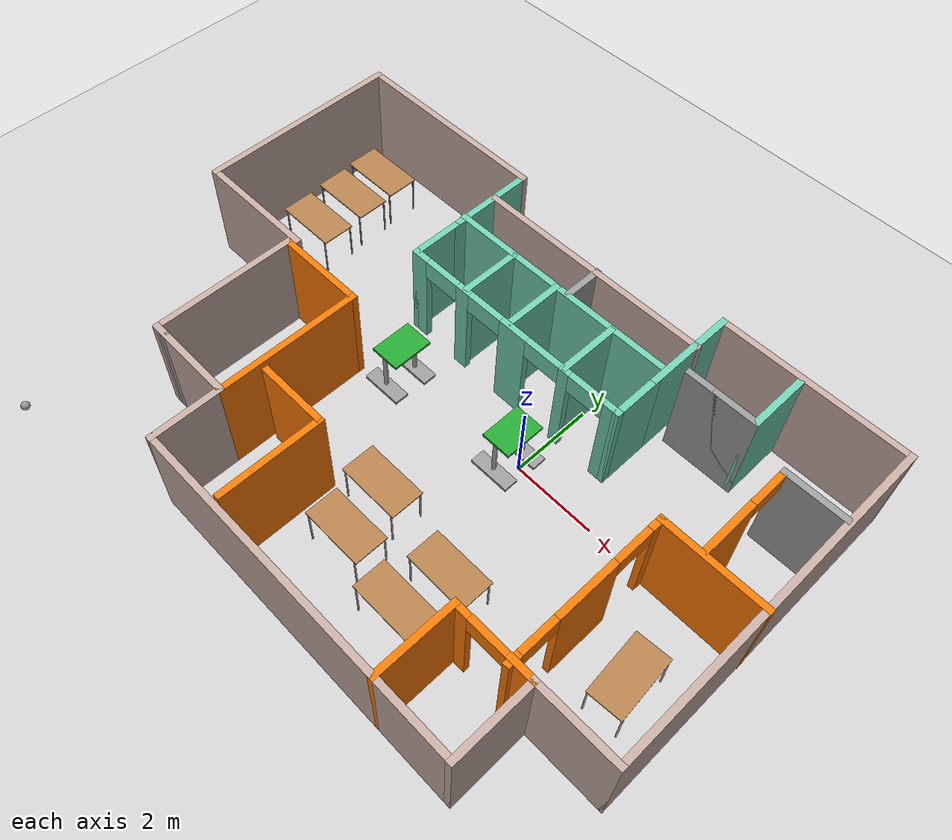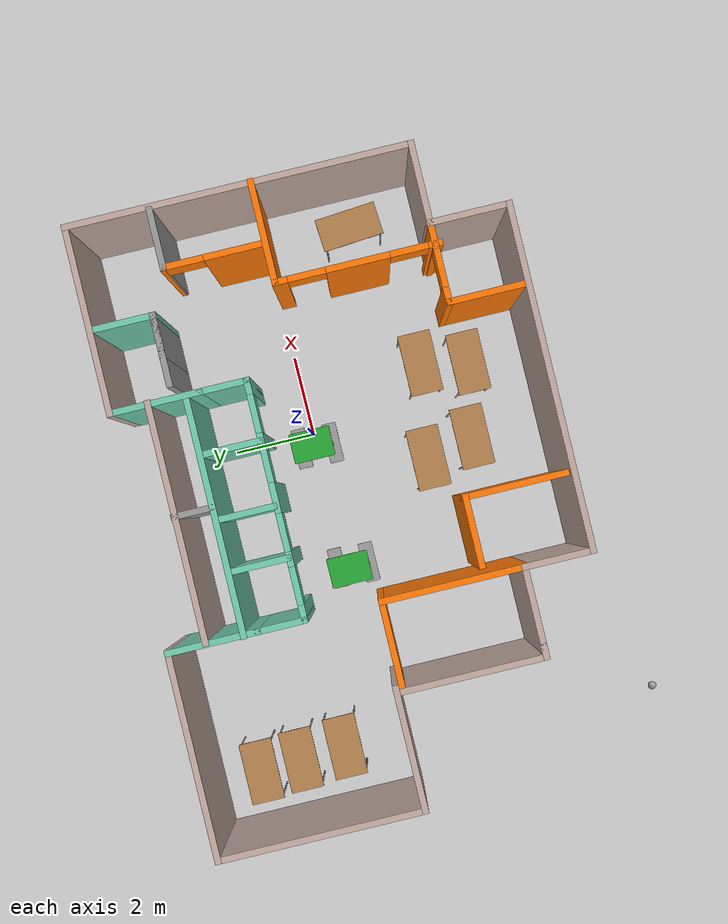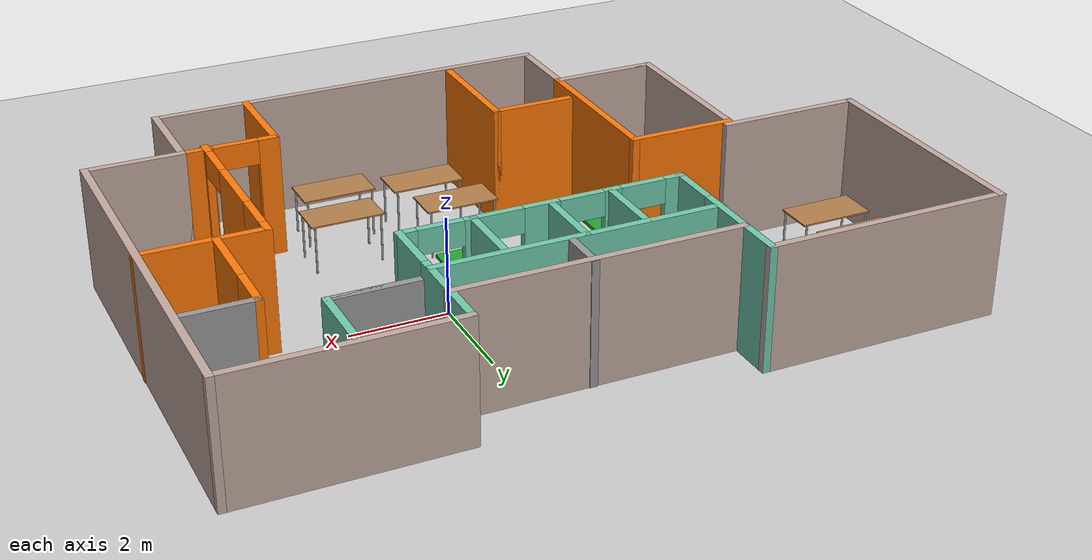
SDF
<sdf version="1.6">
 <world name="default">
  <light name="sun" type="directional">
   <pose>0 0 10 0 -0 0</pose>
   <diffuse>0.8 0.8 0.8 1</diffuse>
   <specular>0.2 0.2 0.2 1</specular>
   <attenuation>
    <range>1000</range>
    <constant>0.9</constant>
    <linear>0.01</linear>
    <quadratic>0.001</quadratic>
   </attenuation>
   <direction>-0.5 0.1 -0.9</direction>
  </light>
  <model name="ground_plane">
   <static>1</static>
   <link name="link">
    <collision name="collision">
     <geometry><plane><normal>0 0 1</normal><size>100 100</size></plane></geometry>
     <surface>
      <contact><collide_bitmask>65535</collide_bitmask></contact>
      <friction><ode><mu>100</mu><mu2>50</mu2></ode></friction>
     </surface>
    </collision>
    <visual name="visual">
     <cast_shadows>0</cast_shadows>
     <geometry><plane><normal>0 0 1</normal><size>100 100</size></plane></geometry>
     <material>
      <script><uri>file://media/materials/scripts/gazebo.material</uri><name>Gazebo/Grey</name></script>
     </material>
    </visual>
   </link>
  </model>
  <gravity>0 0 -9.8</gravity>
  <magnetic_field>6e-06 2.3e-05 -4.2e-05</magnetic_field>
  <atmosphere type="adiabatic"/>
  <physics name="default_physics" default="0" type="ode">
   <max_step_size>0.001</max_step_size>
   <real_time_factor>1</real_time_factor>
   <real_time_update_rate>1000</real_time_update_rate>
  </physics>
  <scene><ambient>0.4 0.4 0.4 1</ambient><background>0.7 0.7 0.7 1</background><shadows>1</shadows></scene>
  <spherical_coordinates>
   <surface_model>EARTH_WGS84</surface_model>
   <latitude_deg>0</latitude_deg>
   <longitude_deg>0</longitude_deg>
   <elevation>0</elevation>
   <heading_deg>0</heading_deg>
  </spherical_coordinates>
  <model name="Building">
   <pose>-1.69632 -0.68623 0 0 -0 0</pose>
   <link name="Wall_0">
    <collision name="Wall_0_Collision">
     <geometry><box><size>8.25 0.15 2.5</size></box></geometry>
     <pose>0 0 1.25 0 -0 0</pose>
    </collision>
    <visual name="Wall_0_Visual">
     <pose>0 0 1.25 0 -0 0</pose>
     <geometry><box><size>8.25 0.15 2.5</size></box></geometry>
     <material>
      <script><uri>file://media/materials/scripts/gazebo.material</uri><name>Gazebo/Grey</name></script>
      <ambient>0.760784 0.662745 0.627451 1</ambient>
     </material>
     <meta><layer>0</layer></meta>
    </visual>
    <pose>1.4941 -4.975 0 0 -0 0</pose>
   </link>
   <link name="Wall_1">
    <collision name="Wall_1_Collision">
     <geometry><box><size>2 0.15 2.5</size></box></geometry>
     <pose>0 0 1.25 0 -0 0</pose>
    </collision>
    <visual name="Wall_1_Visual">
     <pose>0 0 1.25 0 -0 0</pose>
     <geometry><box><size>2 0.15 2.5</size></box></geometry>
     <material>
      <script><uri>file://media/materials/scripts/gazebo.material</uri><name>Gazebo/Grey</name></script>
      <ambient>0.760784 0.662745 0.627451 1</ambient>
     </material>
     <meta><layer>0</layer></meta>
    </visual>
    <pose>5.5441 -4.05 0 0 -0 1.5708</pose>
   </link>
   <link name="Wall_10">
    <collision name="Wall_10_Collision">
     <geometry><box><size>3 0.15 2.5</size></box></geometry>
     <pose>0 0 1.25 0 -0 0</pose>
    </collision>
    <visual name="Wall_10_Visual">
     <pose>0 0 1.25 0 -0 0</pose>
     <geometry><box><size>3 0.15 2.5</size></box></geometry>
     <material>
      <script><uri>file://media/materials/scripts/gazebo.material</uri><name>Gazebo/Grey</name></script>
      <ambient>0.760784 0.662745 0.627451 1</ambient>
     </material>
     <meta><layer>0</layer></meta>
    </visual>
    <pose>-5.9809 0.125 0 0 -0 0</pose>
   </link>
   <link name="Wall_15">
    <pose>4.6191 -3.125 0 0 -0 3.14159</pose>
    <visual name="Wall_15_Visual_0">
     <pose>-0.661107 0 1.25 0 -0 0</pose>
     <geometry><box><size>0.677786 0.15 2.5</size></box></geometry>
     <material>
      <script><uri>file://media/materials/scripts/gazebo.material</uri><name>Gazebo/Grey</name></script>
      <ambient>0.996078 0.47451 0.0196078 1</ambient>
     </material>
     <meta><layer>0</layer></meta>
    </visual>
    <collision name="Wall_15_Collision_0">
     <geometry><box><size>0.677786 0.15 2.5</size></box></geometry>
     <pose>-0.661107 0 1.25 0 -0 0</pose>
    </collision>
    <visual name="Wall_15_Visual_1">
     <pose>0.788893 0 1.25 0 -0 0</pose>
     <geometry><box><size>0.422214 0.15 2.5</size></box></geometry>
     <material>
      <script><uri>file://media/materials/scripts/gazebo.material</uri><name>Gazebo/Grey</name></script>
      <ambient>0.996078 0.47451 0.0196078 1</ambient>
     </material>
     <meta><layer>0</layer></meta>
    </visual>
    <collision name="Wall_15_Collision_1">
     <geometry><box><size>0.422214 0.15 2.5</size></box></geometry>
     <pose>0.788893 0 1.25 0 -0 0</pose>
    </collision>
    <visual name="Wall_15_Visual_2">
     <pose>0.127786 0 2.25 0 -0 0</pose>
     <geometry><box><size>0.9 0.15 0.5</size></box></geometry>
     <material>
      <script><uri>file://media/materials/scripts/gazebo.material</uri><name>Gazebo/Grey</name></script>
      <ambient>0.996078 0.47451 0.0196078 1</ambient>
     </material>
     <meta><layer>0</layer></meta>
    </visual>
    <collision name="Wall_15_Collision_2">
     <geometry><box><size>0.9 0.15 0.5</size></box></geometry>
     <pose>0.127786 0 2.25 0 -0 0</pose>
    </collision>
   </link>
   <link name="Wall_16">
    <collision name="Wall_16_Collision">
     <geometry><box><size>2 0.15 2.5</size></box></geometry>
     <pose>0 0 1.25 0 -0 0</pose>
    </collision>
    <visual name="Wall_16_Visual">
     <pose>0 0 1.25 0 -0 0</pose>
     <geometry><box><size>2 0.15 2.5</size></box></geometry>
     <material>
      <script><uri>file://media/materials/scripts/gazebo.material</uri><name>Gazebo/Grey</name></script>
      <ambient>0.996078 0.47451 0.0196078 1</ambient>
     </material>
     <meta><layer>0</layer></meta>
    </visual>
    <pose>3.6941 -4.05 0 0 0 -1.5708</pose>
   </link>
   <link name="Wall_18">
    <pose>5.0559 -1.30012 0 0 -0 1.5708</pose>
    <visual name="Wall_18_Visual_0">
     <pose>-1.833 0 1.25 0 -0 0</pose>
     <geometry><box><size>0.334005 0.15 2.5</size></box></geometry>
     <material>
      <script><uri>file://media/materials/scripts/gazebo.material</uri><name>Gazebo/Grey</name></script>
      <ambient>0.996078 0.47451 0.0196078 1</ambient>
     </material>
     <meta><layer>0</layer></meta>
    </visual>
    <collision name="Wall_18_Collision_0">
     <geometry><box><size>0.334005 0.15 2.5</size></box></geometry>
     <pose>-1.833 0 1.25 0 -0 0</pose>
    </collision>
    <visual name="Wall_18_Visual_1">
     <pose>-0.013204 0 1.25 0 -0 0</pose>
     <geometry><box><size>1.50558 0.15 2.5</size></box></geometry>
     <material>
      <script><uri>file://media/materials/scripts/gazebo.material</uri><name>Gazebo/Grey</name></script>
      <ambient>0.996078 0.47451 0.0196078 1</ambient>
     </material>
     <meta><layer>0</layer></meta>
    </visual>
    <collision name="Wall_18_Collision_1">
     <geometry><box><size>1.50558 0.15 2.5</size></box></geometry>
     <pose>-0.013204 0 1.25 0 -0 0</pose>
    </collision>
    <visual name="Wall_18_Visual_2">
     <pose>1.81979 0 1.25 0 -0 0</pose>
     <geometry><box><size>0.360412 0.15 2.5</size></box></geometry>
     <material>
      <script><uri>file://media/materials/scripts/gazebo.material</uri><name>Gazebo/Grey</name></script>
      <ambient>0.996078 0.47451 0.0196078 1</ambient>
     </material>
     <meta><layer>0</layer></meta>
    </visual>
    <collision name="Wall_18_Collision_2">
     <geometry><box><size>0.360412 0.15 2.5</size></box></geometry>
     <pose>1.81979 0 1.25 0 -0 0</pose>
    </collision>
    <visual name="Wall_18_Visual_3">
     <pose>-1.21599 0 2.25 0 -0 0</pose>
     <geometry><box><size>0.9 0.15 0.5</size></box></geometry>
     <material>
      <script><uri>file://media/materials/scripts/gazebo.material</uri><name>Gazebo/Grey</name></script>
      <ambient>0.996078 0.47451 0.0196078 1</ambient>
     </material>
     <meta><layer>0</layer></meta>
    </visual>
    <collision name="Wall_18_Collision_3">
     <geometry><box><size>0.9 0.15 0.5</size></box></geometry>
     <pose>-1.21599 0 2.25 0 -0 0</pose>
    </collision>
    <visual name="Wall_18_Visual_4">
     <pose>1.18959 0 2.25 0 -0 0</pose>
     <geometry><box><size>0.9 0.15 0.5</size></box></geometry>
     <material>
      <script><uri>file://media/materials/scripts/gazebo.material</uri><name>Gazebo/Grey</name></script>
      <ambient>0.996078 0.47451 0.0196078 1</ambient>
     </material>
     <meta><layer>0</layer></meta>
    </visual>
    <collision name="Wall_18_Collision_4">
     <geometry><box><size>0.9 0.15 0.5</size></box></geometry>
     <pose>1.18959 0 2.25 0 -0 0</pose>
    </collision>
   </link>
   <link name="Wall_19">
    <collision name="Wall_19_Collision">
     <geometry><box><size>2.5 0.15 2.5</size></box></geometry>
     <pose>0 0 1.25 0 -0 0</pose>
    </collision>
    <visual name="Wall_19_Visual">
     <pose>0 0 1.25 0 -0 0</pose>
     <geometry><box><size>2.5 0.15 2.5</size></box></geometry>
     <material>
      <script><uri>file://media/materials/scripts/gazebo.material</uri><name>Gazebo/Grey</name></script>
      <ambient>0.996078 0.47451 0.0196078 1</ambient>
     </material>
     <meta><layer>0</layer></meta>
    </visual>
    <pose>6.2309 0.624882 0 0 -0 0</pose>
   </link>
   <link name="Wall_2">
    <collision name="Wall_2_Collision">
     <geometry><box><size>2 0.15 2.5</size></box></geometry>
     <pose>0 0 1.25 0 -0 0</pose>
    </collision>
    <visual name="Wall_2_Visual">
     <pose>0 0 1.25 0 -0 0</pose>
     <geometry><box><size>2 0.15 2.5</size></box></geometry>
     <material>
      <script><uri>file://media/materials/scripts/gazebo.material</uri><name>Gazebo/Grey</name></script>
      <ambient>0.760784 0.662745 0.627451 1</ambient>
     </material>
     <meta><layer>0</layer></meta>
    </visual>
    <pose>6.4691 -3.125 0 0 -0 0</pose>
   </link>
   <link name="Wall_21">
    <pose>5.98112 1.83582 0 0 -0 1.5708</pose>
    <visual name="Wall_21_Visual_0">
     <pose>-0.504732 0 1.25 0 -0 0</pose>
     <geometry><box><size>1.49053 0.15 2.5</size></box></geometry>
     <material>
      <script><uri>file://media/materials/scripts/gazebo.material</uri><name>Gazebo/Grey</name></script>
      <ambient>0.996078 0.47451 0.0196078 1</ambient>
     </material>
     <meta><layer>0</layer></meta>
    </visual>
    <collision name="Wall_21_Collision_0">
     <geometry><box><size>1.49053 0.15 2.5</size></box></geometry>
     <pose>-0.504732 0 1.25 0 -0 0</pose>
    </collision>
    <visual name="Wall_21_Visual_1">
     <pose>1.19527 0 1.25 0 -0 0</pose>
     <geometry><box><size>0.109465 0.15 2.5</size></box></geometry>
     <material>
      <script><uri>file://media/materials/scripts/gazebo.material</uri><name>Gazebo/Grey</name></script>
      <ambient>0.996078 0.47451 0.0196078 1</ambient>
     </material>
     <meta><layer>0</layer></meta>
    </visual>
    <collision name="Wall_21_Collision_1">
     <geometry><box><size>0.109465 0.15 2.5</size></box></geometry>
     <pose>1.19527 0 1.25 0 -0 0</pose>
    </collision>
    <visual name="Wall_21_Visual_2">
     <pose>0.690535 0 2.25 0 -0 0</pose>
     <geometry><box><size>0.9 0.15 0.5</size></box></geometry>
     <material>
      <script><uri>file://media/materials/scripts/gazebo.material</uri><name>Gazebo/Grey</name></script>
      <ambient>0.996078 0.47451 0.0196078 1</ambient>
     </material>
     <meta><layer>0</layer></meta>
    </visual>
    <collision name="Wall_21_Collision_2">
     <geometry><box><size>0.9 0.15 0.5</size></box></geometry>
     <pose>0.690535 0 2.25 0 -0 0</pose>
    </collision>
   </link>
   <link name="Wall_22">
    <collision name="Wall_22_Collision">
     <geometry><box><size>1.5 0.15 2.5</size></box></geometry>
     <pose>0 0 1.25 0 -0 0</pose>
    </collision>
    <visual name="Wall_22_Visual">
     <pose>0 0 1.25 0 -0 0</pose>
     <geometry><box><size>1.5 0.15 2.5</size></box></geometry>
     <material>
      <script><uri>file://media/materials/scripts/gazebo.material</uri><name>Gazebo/Grey</name></script>
      <ambient>1 1 1 1</ambient>
     </material>
     <meta><layer>0</layer></meta>
    </visual>
    <pose>6.65612 3.01082 0 0 -0 0</pose>
   </link>
   <link name="Wall_25">
    <collision name="Wall_25_Collision">
     <geometry><box><size>1.75 0.15 2.5</size></box></geometry>
     <pose>0 0 1.25 0 -0 0</pose>
    </collision>
    <visual name="Wall_25_Visual">
     <pose>0 0 1.25 0 -0 0</pose>
     <geometry><box><size>1.75 0.15 2.5</size></box></geometry>
     <material>
      <script><uri>file://media/materials/scripts/gazebo.material</uri><name>Gazebo/Grey</name></script>
      <ambient>0.760784 0.662745 0.627451 1</ambient>
     </material>
     <meta><layer>0</layer></meta>
    </visual>
    <pose>-2.5559 -4.175 0 0 -0 1.5708</pose>
   </link>
   <link name="Wall_27">
    <collision name="Wall_27_Collision">
     <geometry><box><size>0.15 0.15 2.5</size></box></geometry>
     <pose>0 0 1.25 0 -0 0</pose>
    </collision>
    <visual name="Wall_27_Visual">
     <pose>0 0 1.25 0 -0 0</pose>
     <geometry><box><size>0.15 0.15 2.5</size></box></geometry>
     <material>
      <script><uri>file://media/materials/scripts/gazebo.material</uri><name>Gazebo/Grey</name></script>
      <ambient>1 1 1 1</ambient>
     </material>
     <meta><layer>0</layer></meta>
    </visual>
    <pose>-4.4059 -3.375 0 0 -0 0</pose>
   </link>
   <link name="Wall_28">
    <collision name="Wall_28_Collision">
     <geometry><box><size>0.15 0.15 2.5</size></box></geometry>
     <pose>0 0 1.25 0 -0 0</pose>
    </collision>
    <visual name="Wall_28_Visual">
     <pose>0 0 1.25 0 -0 0</pose>
     <geometry><box><size>0.15 0.15 2.5</size></box></geometry>
     <material>
      <script><uri>file://media/materials/scripts/gazebo.material</uri><name>Gazebo/Grey</name></script>
      <ambient>1 1 1 1</ambient>
     </material>
     <meta><layer>0</layer></meta>
    </visual>
    <pose>-4.4059 -3.375 0 0 -0 0</pose>
   </link>
   <link name="Wall_29">
    <collision name="Wall_29_Collision">
     <geometry><box><size>0.15 0.15 2.5</size></box></geometry>
     <pose>0 0 1.25 0 -0 0</pose>
    </collision>
    <visual name="Wall_29_Visual">
     <pose>0 0 1.25 0 -0 0</pose>
     <geometry><box><size>0.15 0.15 2.5</size></box></geometry>
     <material>
      <script><uri>file://media/materials/scripts/gazebo.material</uri><name>Gazebo/Grey</name></script>
      <ambient>1 1 1 1</ambient>
     </material>
     <meta><layer>0</layer></meta>
    </visual>
    <pose>-4.4059 -3.375 0 0 -0 0</pose>
   </link>
   <link name="Wall_3">
    <collision name="Wall_3_Collision">
     <geometry><box><size>8.25 0.15 2.5</size></box></geometry>
     <pose>0 0 1.25 0 -0 0</pose>
    </collision>
    <visual name="Wall_3_Visual">
     <pose>0 0 1.25 0 -0 0</pose>
     <geometry><box><size>8.25 0.15 2.5</size></box></geometry>
     <material>
      <script><uri>file://media/materials/scripts/gazebo.material</uri><name>Gazebo/Grey</name></script>
      <ambient>0.760784 0.662745 0.627451 1</ambient>
     </material>
     <meta><layer>0</layer></meta>
    </visual>
    <pose>7.3941 0.925 0 0 -0 1.5708</pose>
   </link>
   <link name="Wall_30">
    <collision name="Wall_30_Collision">
     <geometry><box><size>0.15 0.15 2.5</size></box></geometry>
     <pose>0 0 1.25 0 -0 0</pose>
    </collision>
    <visual name="Wall_30_Visual">
     <pose>0 0 1.25 0 -0 0</pose>
     <geometry><box><size>0.15 0.15 2.5</size></box></geometry>
     <material>
      <script><uri>file://media/materials/scripts/gazebo.material</uri><name>Gazebo/Grey</name></script>
      <ambient>1 1 1 1</ambient>
     </material>
     <meta><layer>0</layer></meta>
    </visual>
    <pose>-4.4059 -3.375 0 0 -0 0</pose>
   </link>
   <link name="Wall_33">
    <collision name="Wall_33_Collision">
     <geometry><box><size>2.25 0.15 2.5</size></box></geometry>
     <pose>0 0 1.25 0 -0 0</pose>
    </collision>
    <visual name="Wall_33_Visual">
     <pose>0 0 1.25 0 -0 0</pose>
     <geometry><box><size>2.25 0.15 2.5</size></box></geometry>
     <material>
      <script><uri>file://media/materials/scripts/gazebo.material</uri><name>Gazebo/Grey</name></script>
      <ambient>0.760784 0.662745 0.627451 1</ambient>
     </material>
     <meta><layer>0</layer></meta>
    </visual>
    <pose>-3.6059 -3.375 0 0 -0 3.14159</pose>
   </link>
   <link name="Wall_34">
    <collision name="Wall_34_Collision">
     <geometry><box><size>3.5 0.15 2.5</size></box></geometry>
     <pose>0 0 1.25 0 -0 0</pose>
    </collision>
    <visual name="Wall_34_Visual">
     <pose>0 0 1.25 0 -0 0</pose>
     <geometry><box><size>3.5 0.15 2.5</size></box></geometry>
     <material>
      <script><uri>file://media/materials/scripts/gazebo.material</uri><name>Gazebo/Grey</name></script>
      <ambient>0.760784 0.662745 0.627451 1</ambient>
     </material>
     <meta><layer>0</layer></meta>
    </visual>
    <pose>-4.6559 -1.7 0 0 -0 1.5708</pose>
   </link>
   <link name="Wall_39">
    <collision name="Wall_39_Collision">
     <geometry><box><size>3.5 0.15 2.5</size></box></geometry>
     <pose>0 0 1.25 0 -0 0</pose>
    </collision>
    <visual name="Wall_39_Visual">
     <pose>0 0 1.25 0 -0 0</pose>
     <geometry><box><size>3.5 0.15 2.5</size></box></geometry>
     <material>
      <script><uri>file://media/materials/scripts/gazebo.material</uri><name>Gazebo/Grey</name></script>
      <ambient>0.996078 0.47451 0.0196078 1</ambient>
     </material>
     <meta><layer>0</layer></meta>
    </visual>
    <pose>-2.5559 -1.7 0 0 -0 1.5708</pose>
   </link>
   <link name="Wall_4">
    <collision name="Wall_4_Collision">
     <geometry><box><size>4.5 0.15 2.5</size></box></geometry>
     <pose>0 0 1.25 0 -0 0</pose>
    </collision>
    <visual name="Wall_4_Visual">
     <pose>0 0 1.25 0 -0 0</pose>
     <geometry><box><size>4.5 0.15 2.5</size></box></geometry>
     <material>
      <script><uri>file://media/materials/scripts/gazebo.material</uri><name>Gazebo/Grey</name></script>
      <ambient>0.760784 0.662745 0.627451 1</ambient>
     </material>
     <meta><layer>0</layer></meta>
    </visual>
    <pose>5.2191 4.975 0 0 -0 3.14159</pose>
   </link>
   <link name="Wall_40">
    <collision name="Wall_40_Collision">
     <geometry><box><size>2.25 0.15 2.5</size></box></geometry>
     <pose>0 0 1.25 0 -0 0</pose>
    </collision>
    <visual name="Wall_40_Visual">
     <pose>0 0 1.25 0 -0 0</pose>
     <geometry><box><size>2.25 0.15 2.5</size></box></geometry>
     <material>
      <script><uri>file://media/materials/scripts/gazebo.material</uri><name>Gazebo/Grey</name></script>
      <ambient>0.996078 0.47451 0.0196078 1</ambient>
     </material>
     <meta><layer>0</layer></meta>
    </visual>
    <pose>-3.6059 -0.025 0 0 -0 3.14159</pose>
   </link>
   <link name="Wall_42">
    <collision name="Wall_42_Collision">
     <geometry><box><size>1.75 0.15 2.5</size></box></geometry>
     <pose>0 0 1.25 0 -0 0</pose>
    </collision>
    <visual name="Wall_42_Visual">
     <pose>0 0 1.25 0 -0 0</pose>
     <geometry><box><size>1.75 0.15 2.5</size></box></geometry>
     <material>
      <script><uri>file://media/materials/scripts/gazebo.material</uri><name>Gazebo/Grey</name></script>
      <ambient>0.996078 0.47451 0.0196078 1</ambient>
     </material>
     <meta><layer>0</layer></meta>
    </visual>
    <pose>-1.49964 -2.43868 0 0 -0 0</pose>
   </link>
   <link name="Wall_43">
    <collision name="Wall_43_Collision">
     <geometry><box><size>2.5 0.15 2.5</size></box></geometry>
     <pose>0 0 1.25 0 -0 0</pose>
    </collision>
    <visual name="Wall_43_Visual">
     <pose>0 0 1.25 0 -0 0</pose>
     <geometry><box><size>2.5 0.15 2.5</size></box></geometry>
     <material>
      <script><uri>file://media/materials/scripts/gazebo.material</uri><name>Gazebo/Grey</name></script>
      <ambient>0.996078 0.47451 0.0196078 1</ambient>
     </material>
     <meta><layer>0</layer></meta>
    </visual>
    <pose>-0.699636 -3.61368 0 0 0 -1.5708</pose>
   </link>
   <link name="Wall_45">
    <collision name="Wall_45_Collision">
     <geometry><box><size>1.25 0.15 2.5</size></box></geometry>
     <pose>0 0 1.25 0 -0 0</pose>
    </collision>
    <visual name="Wall_45_Visual">
     <pose>0 0 1.25 0 -0 0</pose>
     <geometry><box><size>1.25 0.15 2.5</size></box></geometry>
     <material>
      <script><uri>file://media/materials/scripts/gazebo.material</uri><name>Gazebo/Grey</name></script>
      <ambient>0.435294 0.796078 0.67451 1</ambient>
     </material>
     <meta><layer>0</layer></meta>
    </visual>
    <pose>-2.5559 2.325 0 0 0 -1.5708</pose>
   </link>
   <link name="Wall_46">
    <pose>0.244104 1.775 0 0 -0 0</pose>
    <visual name="Wall_46_Visual_0">
     <pose>-2.66153 0 1.25 0 -0 0</pose>
     <geometry><box><size>0.42695 0.15 2.5</size></box></geometry>
     <material>
      <script><uri>file://media/materials/scripts/gazebo.material</uri><name>Gazebo/Grey</name></script>
      <ambient>0.435294 0.796078 0.67451 1</ambient>
     </material>
     <meta><layer>0</layer></meta>
    </visual>
    <collision name="Wall_46_Collision_0">
     <geometry><box><size>0.42695 0.15 2.5</size></box></geometry>
     <pose>-2.66153 0 1.25 0 -0 0</pose>
    </collision>
    <visual name="Wall_46_Visual_1">
     <pose>-1.37352 0 1.25 0 -0 0</pose>
     <geometry><box><size>0.349053 0.15 2.5</size></box></geometry>
     <material>
      <script><uri>file://media/materials/scripts/gazebo.material</uri><name>Gazebo/Grey</name></script>
      <ambient>0.435294 0.796078 0.67451 1</ambient>
     </material>
     <meta><layer>0</layer></meta>
    </visual>
    <collision name="Wall_46_Collision_1">
     <geometry><box><size>0.349053 0.15 2.5</size></box></geometry>
     <pose>-1.37352 0 1.25 0 -0 0</pose>
    </collision>
    <visual name="Wall_46_Visual_2">
     <pose>0.060574 0 1.25 0 -0 0</pose>
     <geometry><box><size>0.719143 0.15 2.5</size></box></geometry>
     <material>
      <script><uri>file://media/materials/scripts/gazebo.material</uri><name>Gazebo/Grey</name></script>
      <ambient>0.435294 0.796078 0.67451 1</ambient>
     </material>
     <meta><layer>0</layer></meta>
    </visual>
    <collision name="Wall_46_Collision_2">
     <geometry><box><size>0.719143 0.15 2.5</size></box></geometry>
     <pose>0.060574 0 1.25 0 -0 0</pose>
    </collision>
    <visual name="Wall_46_Visual_3">
     <pose>1.44841 0 1.25 0 -0 0</pose>
     <geometry><box><size>0.25653 0.15 2.5</size></box></geometry>
     <material>
      <script><uri>file://media/materials/scripts/gazebo.material</uri><name>Gazebo/Grey</name></script>
      <ambient>0.435294 0.796078 0.67451 1</ambient>
     </material>
     <meta><layer>0</layer></meta>
    </visual>
    <collision name="Wall_46_Collision_3">
     <geometry><box><size>0.25653 0.15 2.5</size></box></geometry>
     <pose>1.44841 0 1.25 0 -0 0</pose>
    </collision>
    <visual name="Wall_46_Visual_4">
     <pose>2.67584 0 1.25 0 -0 0</pose>
     <geometry><box><size>0.398324 0.15 2.5</size></box></geometry>
     <material>
      <script><uri>file://media/materials/scripts/gazebo.material</uri><name>Gazebo/Grey</name></script>
      <ambient>0.435294 0.796078 0.67451 1</ambient>
     </material>
     <meta><layer>0</layer></meta>
    </visual>
    <collision name="Wall_46_Collision_4">
     <geometry><box><size>0.398324 0.15 2.5</size></box></geometry>
     <pose>2.67584 0 1.25 0 -0 0</pose>
    </collision>
    <visual name="Wall_46_Visual_5">
     <pose>-1.99805 0 2.25 0 -0 0</pose>
     <geometry><box><size>0.9 0.15 0.5</size></box></geometry>
     <material>
      <script><uri>file://media/materials/scripts/gazebo.material</uri><name>Gazebo/Grey</name></script>
      <ambient>0.435294 0.796078 0.67451 1</ambient>
     </material>
     <meta><layer>0</layer></meta>
    </visual>
    <collision name="Wall_46_Collision_5">
     <geometry><box><size>0.9 0.15 0.5</size></box></geometry>
     <pose>-1.99805 0 2.25 0 -0 0</pose>
    </collision>
    <visual name="Wall_46_Visual_6">
     <pose>-0.748997 0 2.25 0 -0 0</pose>
     <geometry><box><size>0.9 0.15 0.5</size></box></geometry>
     <material>
      <script><uri>file://media/materials/scripts/gazebo.material</uri><name>Gazebo/Grey</name></script>
      <ambient>0.435294 0.796078 0.67451 1</ambient>
     </material>
     <meta><layer>0</layer></meta>
    </visual>
    <collision name="Wall_46_Collision_6">
     <geometry><box><size>0.9 0.15 0.5</size></box></geometry>
     <pose>-0.748997 0 2.25 0 -0 0</pose>
    </collision>
    <visual name="Wall_46_Visual_7">
     <pose>0.870145 0 2.25 0 -0 0</pose>
     <geometry><box><size>0.9 0.15 0.5</size></box></geometry>
     <material>
      <script><uri>file://media/materials/scripts/gazebo.material</uri><name>Gazebo/Grey</name></script>
      <ambient>0.435294 0.796078 0.67451 1</ambient>
     </material>
     <meta><layer>0</layer></meta>
    </visual>
    <collision name="Wall_46_Collision_7">
     <geometry><box><size>0.9 0.15 0.5</size></box></geometry>
     <pose>0.870145 0 2.25 0 -0 0</pose>
    </collision>
    <visual name="Wall_46_Visual_8">
     <pose>2.02668 0 2.25 0 -0 0</pose>
     <geometry><box><size>0.9 0.15 0.5</size></box></geometry>
     <material>
      <script><uri>file://media/materials/scripts/gazebo.material</uri><name>Gazebo/Grey</name></script>
      <ambient>0.435294 0.796078 0.67451 1</ambient>
     </material>
     <meta><layer>0</layer></meta>
    </visual>
    <collision name="Wall_46_Collision_8">
     <geometry><box><size>0.9 0.15 0.5</size></box></geometry>
     <pose>2.02668 0 2.25 0 -0 0</pose>
    </collision>
   </link>
   <link name="Wall_47">
    <collision name="Wall_47_Collision">
     <geometry><box><size>1.25 0.15 2.5</size></box></geometry>
     <pose>0 0 1.25 0 -0 0</pose>
    </collision>
    <visual name="Wall_47_Visual">
     <pose>0 0 1.25 0 -0 0</pose>
     <geometry><box><size>1.25 0.15 2.5</size></box></geometry>
     <material>
      <script><uri>file://media/materials/scripts/gazebo.material</uri><name>Gazebo/Grey</name></script>
      <ambient>0.435294 0.796078 0.67451 1</ambient>
     </material>
     <meta><layer>0</layer></meta>
    </visual>
    <pose>3.0441 2.325 0 0 -0 1.5708</pose>
   </link>
   <link name="Wall_49">
    <collision name="Wall_49_Collision">
     <geometry><box><size>5.75 0.15 2.5</size></box></geometry>
     <pose>0 0 1.25 0 -0 0</pose>
    </collision>
    <visual name="Wall_49_Visual">
     <pose>0 0 1.25 0 -0 0</pose>
     <geometry><box><size>5.75 0.15 2.5</size></box></geometry>
     <material>
      <script><uri>file://media/materials/scripts/gazebo.material</uri><name>Gazebo/Grey</name></script>
      <ambient>0.760784 0.662745 0.627451 1</ambient>
     </material>
     <meta><layer>0</layer></meta>
    </visual>
    <pose>0.269058 4.08415 0 0 -0 0</pose>
   </link>
   <link name="Wall_5">
    <collision name="Wall_5_Collision">
     <geometry><box><size>2.25 0.15 2.5</size></box></geometry>
     <pose>0 0 1.25 0 -0 0</pose>
    </collision>
    <visual name="Wall_5_Visual">
     <pose>0 0 1.25 0 -0 0</pose>
     <geometry><box><size>2.25 0.15 2.5</size></box></geometry>
     <material>
      <script><uri>file://media/materials/scripts/gazebo.material</uri><name>Gazebo/Grey</name></script>
      <ambient>0.435294 0.796078 0.67451 1</ambient>
     </material>
     <meta><layer>0</layer></meta>
    </visual>
    <pose>3.0441 3.925 0 0 0 -1.5708</pose>
   </link>
   <link name="Wall_53">
    <collision name="Wall_53_Collision">
     <geometry><box><size>5.75 0.15 2.5</size></box></geometry>
     <pose>0 0 1.25 0 -0 0</pose>
    </collision>
    <visual name="Wall_53_Visual">
     <pose>0 0 1.25 0 -0 0</pose>
     <geometry><box><size>5.75 0.15 2.5</size></box></geometry>
     <material>
      <script><uri>file://media/materials/scripts/gazebo.material</uri><name>Gazebo/Grey</name></script>
      <ambient>0.435294 0.796078 0.67451 1</ambient>
     </material>
     <meta><layer>0</layer></meta>
    </visual>
    <pose>0.222797 3.20519 0 0 -0 0</pose>
   </link>
   <link name="Wall_58">
    <collision name="Wall_58_Collision">
     <geometry><box><size>1 0.15 2.5</size></box></geometry>
     <pose>0 0 1.25 0 -0 0</pose>
    </collision>
    <visual name="Wall_58_Visual">
     <pose>0 0 1.25 0 -0 0</pose>
     <geometry><box><size>1 0.15 2.5</size></box></geometry>
     <material>
      <script><uri>file://media/materials/scripts/gazebo.material</uri><name>Gazebo/Grey</name></script>
      <ambient>1 1 1 1</ambient>
     </material>
     <meta><layer>0</layer></meta>
    </visual>
    <pose>0.425617 3.67936 0 0 0 -1.5708</pose>
   </link>
   <link name="Wall_65">
    <collision name="Wall_65_Collision">
     <geometry><box><size>1.5 0.15 2.5</size></box></geometry>
     <pose>0 0 1.25 0 -0 0</pose>
    </collision>
    <visual name="Wall_65_Visual">
     <pose>0 0 1.25 0 -0 0</pose>
     <geometry><box><size>1.5 0.15 2.5</size></box></geometry>
     <material>
      <script><uri>file://media/materials/scripts/gazebo.material</uri><name>Gazebo/Grey</name></script>
      <ambient>0.435294 0.796078 0.67451 1</ambient>
     </material>
     <meta><layer>0</layer></meta>
    </visual>
    <pose>-1.09526 2.48642 0 0 0 -1.5708</pose>
   </link>
   <link name="Wall_67">
    <collision name="Wall_67_Collision">
     <geometry><box><size>1.5 0.15 2.5</size></box></geometry>
     <pose>0 0 1.25 0 -0 0</pose>
    </collision>
    <visual name="Wall_67_Visual">
     <pose>0 0 1.25 0 -0 0</pose>
     <geometry><box><size>1.5 0.15 2.5</size></box></geometry>
     <material>
      <script><uri>file://media/materials/scripts/gazebo.material</uri><name>Gazebo/Grey</name></script>
      <ambient>0.435294 0.796078 0.67451 1</ambient>
     </material>
     <meta><layer>0</layer></meta>
    </visual>
    <pose>0.121442 2.51684 0 0 0 -1.5708</pose>
   </link>
   <link name="Wall_69">
    <collision name="Wall_69_Collision">
     <geometry><box><size>1.5 0.15 2.5</size></box></geometry>
     <pose>0 0 1.25 0 -0 0</pose>
    </collision>
    <visual name="Wall_69_Visual">
     <pose>0 0 1.25 0 -0 0</pose>
     <geometry><box><size>1.5 0.15 2.5</size></box></geometry>
     <material>
      <script><uri>file://media/materials/scripts/gazebo.material</uri><name>Gazebo/Grey</name></script>
      <ambient>0.435294 0.796078 0.67451 1</ambient>
     </material>
     <meta><layer>0</layer></meta>
    </visual>
    <pose>1.64232 2.48642 0 0 0 -1.5708</pose>
   </link>
   <link name="Wall_7">
    <collision name="Wall_7_Collision">
     <geometry><box><size>2.25 0.15 2.5</size></box></geometry>
     <pose>0 0 1.25 0 -0 0</pose>
    </collision>
    <visual name="Wall_7_Visual">
     <pose>0 0 1.25 0 -0 0</pose>
     <geometry><box><size>2.25 0.15 2.5</size></box></geometry>
     <material>
      <script><uri>file://media/materials/scripts/gazebo.material</uri><name>Gazebo/Grey</name></script>
      <ambient>0.435294 0.796078 0.67451 1</ambient>
     </material>
     <meta><layer>0</layer></meta>
    </visual>
    <pose>-2.5559 3.925 0 0 -0 1.5708</pose>
   </link>
   <link name="Wall_71">
    <pose>4.18105 3.49784 0 0 -0 0</pose>
    <visual name="Wall_71_Visual_0">
     <pose>0 0 1.25 0 -0 0</pose>
     <geometry><box><size>1.75 0.15 2.5</size></box></geometry>
     <material>
      <script><uri>file://media/materials/scripts/gazebo.material</uri><name>Gazebo/Grey</name></script>
      <ambient>1 1 1 1</ambient>
     </material>
     <meta><layer>0</layer></meta>
    </visual>
    <collision name="Wall_71_Collision_0">
     <geometry><box><size>1.75 0.15 2.5</size></box></geometry>
     <pose>0 0 1.25 0 -0 0</pose>
    </collision>
    <visual name="Wall_71_Visual_1">
     <pose>0.331892 0 1.25 0 -0 0</pose>
     <geometry><box><size>1.08622 0.15 2.5</size></box></geometry>
     <material>
      <script><uri>file://media/materials/scripts/gazebo.material</uri><name>Gazebo/Grey</name></script>
      <ambient>1 1 1 1</ambient>
     </material>
     <meta><layer>0</layer></meta>
    </visual>
    <collision name="Wall_71_Collision_1">
     <geometry><box><size>1.08622 0.15 2.5</size></box></geometry>
     <pose>0.331892 0 1.25 0 -0 0</pose>
    </collision>
   </link>
   <link name="Wall_72">
    <collision name="Wall_72_Collision">
     <geometry><box><size>1.5 0.15 2.5</size></box></geometry>
     <pose>0 0 1.25 0 -0 0</pose>
    </collision>
    <visual name="Wall_72_Visual">
     <pose>0 0 1.25 0 -0 0</pose>
     <geometry><box><size>1.5 0.15 2.5</size></box></geometry>
     <material>
      <script><uri>file://media/materials/scripts/gazebo.material</uri><name>Gazebo/Grey</name></script>
      <ambient>0.435294 0.796078 0.67451 1</ambient>
     </material>
     <meta><layer>0</layer></meta>
    </visual>
    <pose>4.98105 4.17284 0 0 -0 1.5708</pose>
   </link>
   <link name="Wall_8">
    <collision name="Wall_8_Collision">
     <geometry><box><size>5 0.15 2.5</size></box></geometry>
     <pose>0 0 1.25 0 -0 0</pose>
    </collision>
    <visual name="Wall_8_Visual">
     <pose>0 0 1.25 0 -0 0</pose>
     <geometry><box><size>5 0.15 2.5</size></box></geometry>
     <material>
      <script><uri>file://media/materials/scripts/gazebo.material</uri><name>Gazebo/Grey</name></script>
      <ambient>0.760784 0.662745 0.627451 1</ambient>
     </material>
     <meta><layer>0</layer></meta>
    </visual>
    <pose>-4.9809 4.975 0 0 -0 3.14159</pose>
   </link>
   <link name="Wall_9">
    <collision name="Wall_9_Collision">
     <geometry><box><size>5 0.15 2.5</size></box></geometry>
     <pose>0 0 1.25 0 -0 0</pose>
    </collision>
    <visual name="Wall_9_Visual">
     <pose>0 0 1.25 0 -0 0</pose>
     <geometry><box><size>5 0.15 2.5</size></box></geometry>
     <material>
      <script><uri>file://media/materials/scripts/gazebo.material</uri><name>Gazebo/Grey</name></script>
      <ambient>0.760784 0.662745 0.627451 1</ambient>
     </material>
     <meta><layer>0</layer></meta>
    </visual>
    <pose>-7.4059 2.55 0 0 0 -1.5708</pose>
   </link>
   <static>1</static>
  </model>
  <model name="Humanoid">
   <link name="link_0">
    <pose>-0.00782 0.058578 0.612544 0 -0 0</pose>
    <inertial>
     <mass>0.0487032</mass>
     <inertia>
      <ixx>0.00407692</ixx>
      <ixy>0</ixy>
      <ixz>0</ixz>
      <iyy>0.00215077</iyy>
      <iyz>0</iyz>
      <izz>0.00619105</izz>
     </inertia>
    </inertial>
    <visual name="visual">
     <geometry><box><size>0.724854 1 0.067191</size></box></geometry>
     <material>
      <lighting>1</lighting>
      <script><uri>file://media/materials/scripts/gazebo.material</uri><name>Gazebo/Green</name></script>
      <shader type="pixel"/>
      <ambient>0 1 0 1</ambient>
      <diffuse>0 1 0 1</diffuse>
      <specular>0 1 0 1</specular>
      <emissive>0 1 0 1</emissive>
     </material>
    </visual>
    <collision name="collision">
     <geometry><box><size>0.724854 1 0.067191</size></box></geometry>
     <surface>
      <friction>
       <ode><mu>1</mu><mu2>1</mu2><fdir1>0 0 0</fdir1><slip1>0</slip1><slip2>0</slip2></ode>
       <torsional>
        <coefficient>1</coefficient>
        <patch_radius>0</patch_radius>
        <surface_radius>0</surface_radius>
        <use_patch_radius>1</use_patch_radius>
        <ode><slip>0</slip></ode>
       </torsional>
      </friction>
      <bounce><restitution_coefficient>0</restitution_coefficient><threshold>1e+06</threshold></bounce>
      <contact>
       <collide_without_contact>0</collide_without_contact>
       <collide_without_contact_bitmask>1</collide_without_contact_bitmask>
       <collide_bitmask>1</collide_bitmask>
       <ode>
        <soft_cfm>0</soft_cfm>
        <soft_erp>0.2</soft_erp>
        <kp>1e+13</kp>
        <kd>1</kd>
        <max_vel>0.01</max_vel>
        <min_depth>0</min_depth>
       </ode>
       <bullet>
        <split_impulse>1</split_impulse>
        <split_impulse_penetration_threshold>-0.01</split_impulse_penetration_threshold>
        <soft_cfm>0</soft_cfm>
        <soft_erp>0.2</soft_erp>
        <kp>1e+13</kp>
        <kd>1</kd>
       </bullet>
      </contact>
     </surface>
    </collision>
   </link>
   <link name="link_1">
    <pose>-0.00782 -0.422569 -0.385222 0 -0 0</pose>
    <inertial>
     <mass>0.0249491</mass>
     <inertia>
      <ixx>0.00026268</ixx>
      <ixy>0</ixy>
      <ixz>0</ixz>
      <iyy>0.00208977</iyy>
      <iyz>0</iyz>
      <izz>0.00233109</izz>
     </inertia>
    </inertial>
    <visual name="visual">
     <geometry><box><size>1 0.348151 0.071658</size></box></geometry>
     <material>
      <lighting>1</lighting>
      <script><uri>file://media/materials/scripts/gazebo.material</uri><name>Gazebo/Grey</name></script>
      <shader type="pixel"/>
      <ambient>0.3 0.3 0.3 1</ambient>
      <diffuse>0.7 0.7 0.7 1</diffuse>
      <specular>0.01 0.01 0.01 1</specular>
      <emissive>0 0 0 1</emissive>
     </material>
    </visual>
    <collision name="collision">
     <geometry><box><size>1 0.348151 0.071658</size></box></geometry>
     <surface>
      <friction>
       <ode><mu>1</mu><mu2>1</mu2><fdir1>0 0 0</fdir1><slip1>0</slip1><slip2>0</slip2></ode>
       <torsional>
        <coefficient>1</coefficient>
        <patch_radius>0</patch_radius>
        <surface_radius>0</surface_radius>
        <use_patch_radius>1</use_patch_radius>
        <ode><slip>0</slip></ode>
       </torsional>
      </friction>
      <bounce><restitution_coefficient>0</restitution_coefficient><threshold>1e+06</threshold></bounce>
      <contact>
       <collide_without_contact>0</collide_without_contact>
       <collide_without_contact_bitmask>1</collide_without_contact_bitmask>
       <collide_bitmask>1</collide_bitmask>
       <ode>
        <soft_cfm>0</soft_cfm>
        <soft_erp>0.2</soft_erp>
        <kp>1e+13</kp>
        <kd>1</kd>
        <max_vel>0.01</max_vel>
        <min_depth>0</min_depth>
       </ode>
       <bullet>
        <split_impulse>1</split_impulse>
        <split_impulse_penetration_threshold>-0.01</split_impulse_penetration_threshold>
        <soft_cfm>0</soft_cfm>
        <soft_erp>0.2</soft_erp>
        <kp>1e+13</kp>
        <kd>1</kd>
       </bullet>
      </contact>
     </surface>
    </collision>
   </link>
   <link name="link_1_clone">
    <pose>0.033496 0.376243 -0.385222 0 -0 0</pose>
    <inertial>
     <mass>0.0249491</mass>
     <inertia>
      <ixx>0.00026268</ixx>
      <ixy>0</ixy>
      <ixz>0</ixz>
      <iyy>0.00208977</iyy>
      <iyz>0</iyz>
      <izz>0.00233109</izz>
     </inertia>
    </inertial>
    <visual name="visual">
     <geometry><box><size>1 0.348151 0.071658</size></box></geometry>
     <material>
      <lighting>1</lighting>
      <script><uri>file://media/materials/scripts/gazebo.material</uri><name>Gazebo/Grey</name></script>
      <shader type="pixel"/>
      <ambient>0.3 0.3 0.3 1</ambient>
      <diffuse>0.7 0.7 0.7 1</diffuse>
      <specular>0.01 0.01 0.01 1</specular>
      <emissive>0 0 0 1</emissive>
     </material>
    </visual>
    <collision name="collision">
     <geometry><box><size>1 0.348151 0.071658</size></box></geometry>
     <surface>
      <friction>
       <ode><mu>1</mu><mu2>1</mu2><fdir1>0 0 0</fdir1><slip1>0</slip1><slip2>0</slip2></ode>
       <torsional>
        <coefficient>1</coefficient>
        <patch_radius>0</patch_radius>
        <surface_radius>0</surface_radius>
        <use_patch_radius>1</use_patch_radius>
        <ode><slip>0</slip></ode>
       </torsional>
      </friction>
      <bounce><restitution_coefficient>0</restitution_coefficient><threshold>1e+06</threshold></bounce>
      <contact>
       <collide_without_contact>0</collide_without_contact>
       <collide_without_contact_bitmask>1</collide_without_contact_bitmask>
       <collide_bitmask>1</collide_bitmask>
       <ode>
        <soft_cfm>0</soft_cfm>
        <soft_erp>0.2</soft_erp>
        <kp>1e+13</kp>
        <kd>1</kd>
        <max_vel>0.01</max_vel>
        <min_depth>0</min_depth>
       </ode>
       <bullet>
        <split_impulse>1</split_impulse>
        <split_impulse_penetration_threshold>-0.01</split_impulse_penetration_threshold>
        <soft_cfm>0</soft_cfm>
        <soft_erp>0.2</soft_erp>
        <kp>1e+13</kp>
        <kd>1</kd>
       </bullet>
      </contact>
     </surface>
    </collision>
   </link>
   <link name="link_2">
    <pose>-0.051356 -0.388494 0.078949 0 -0 0</pose>
    <inertial>
     <mass>0.0112059</mass>
     <inertia>
      <ixx>0.000941673</ixx>
      <ixy>0</ixy>
      <ixz>0</ixz>
      <iyy>0.000941673</iyy>
      <iyz>0</iyz>
      <izz>1.56964e-05</izz>
     </inertia>
    </inertial>
    <visual name="visual">
     <geometry><cylinder><radius>0.0529288</radius><length>1</length></cylinder></geometry>
     <material>
      <lighting>1</lighting>
      <script><uri>file://media/materials/scripts/gazebo.material</uri><name>Gazebo/Grey</name></script>
      <shader type="pixel"/>
      <ambient>0.3 0.3 0.3 1</ambient>
      <diffuse>0.7 0.7 0.7 1</diffuse>
      <specular>0.01 0.01 0.01 1</specular>
      <emissive>0 0 0 1</emissive>
     </material>
    </visual>
    <collision name="collision">
     <geometry><cylinder><radius>0.052929</radius><length>1</length></cylinder></geometry>
     <surface>
      <friction>
       <ode><mu>1</mu><mu2>1</mu2><fdir1>0 0 0</fdir1><slip1>0</slip1><slip2>0</slip2></ode>
       <torsional>
        <coefficient>1</coefficient>
        <patch_radius>0</patch_radius>
        <surface_radius>0</surface_radius>
        <use_patch_radius>1</use_patch_radius>
        <ode><slip>0</slip></ode>
       </torsional>
      </friction>
      <bounce><restitution_coefficient>0</restitution_coefficient><threshold>1e+06</threshold></bounce>
      <contact>
       <collide_without_contact>0</collide_without_contact>
       <collide_without_contact_bitmask>1</collide_without_contact_bitmask>
       <collide_bitmask>1</collide_bitmask>
       <ode>
        <soft_cfm>0</soft_cfm>
        <soft_erp>0.2</soft_erp>
        <kp>1e+13</kp>
        <kd>1</kd>
        <max_vel>0.01</max_vel>
        <min_depth>0</min_depth>
       </ode>
       <bullet>
        <split_impulse>1</split_impulse>
        <split_impulse_penetration_threshold>-0.01</split_impulse_penetration_threshold>
        <soft_cfm>0</soft_cfm>
        <soft_erp>0.2</soft_erp>
        <kp>1e+13</kp>
        <kd>1</kd>
       </bullet>
      </contact>
     </surface>
    </collision>
   </link>
   <link name="link_2_clone">
    <pose>0.033496 0.376243 0.078949 0 -0 0</pose>
    <inertial>
     <mass>0.0112059</mass>
     <inertia>
      <ixx>0.000941673</ixx>
      <ixy>0</ixy>
      <ixz>0</ixz>
      <iyy>0.000941673</iyy>
      <iyz>0</iyz>
      <izz>1.56964e-05</izz>
     </inertia>
    </inertial>
    <visual name="visual">
     <geometry><cylinder><radius>0.0529288</radius><length>1</length></cylinder></geometry>
     <material>
      <lighting>1</lighting>
      <script><uri>file://media/materials/scripts/gazebo.material</uri><name>Gazebo/Grey</name></script>
      <shader type="pixel"/>
      <ambient>0.3 0.3 0.3 1</ambient>
      <diffuse>0.7 0.7 0.7 1</diffuse>
      <specular>0.01 0.01 0.01 1</specular>
      <emissive>0 0 0 1</emissive>
     </material>
    </visual>
    <collision name="collision">
     <geometry><cylinder><radius>0.052929</radius><length>1</length></cylinder></geometry>
     <surface>
      <friction>
       <ode><mu>1</mu><mu2>1</mu2><fdir1>0 0 0</fdir1><slip1>0</slip1><slip2>0</slip2></ode>
       <torsional>
        <coefficient>1</coefficient>
        <patch_radius>0</patch_radius>
        <surface_radius>0</surface_radius>
        <use_patch_radius>1</use_patch_radius>
        <ode><slip>0</slip></ode>
       </torsional>
      </friction>
      <bounce><restitution_coefficient>0</restitution_coefficient><threshold>1e+06</threshold></bounce>
      <contact>
       <collide_without_contact>0</collide_without_contact>
       <collide_without_contact_bitmask>1</collide_without_contact_bitmask>
       <collide_bitmask>1</collide_bitmask>
       <ode>
        <soft_cfm>0</soft_cfm>
        <soft_erp>0.2</soft_erp>
        <kp>1e+13</kp>
        <kd>1</kd>
        <max_vel>0.01</max_vel>
        <min_depth>0</min_depth>
       </ode>
       <bullet>
        <split_impulse>1</split_impulse>
        <split_impulse_penetration_threshold>-0.01</split_impulse_penetration_threshold>
        <soft_cfm>0</soft_cfm>
        <soft_erp>0.2</soft_erp>
        <kp>1e+13</kp>
        <kd>1</kd>
       </bullet>
      </contact>
     </surface>
    </collision>
   </link>
   <joint name="link_1_JOINT_0" type="fixed">
    <parent>link_1</parent>
    <child>link_2</child>
    <physics>
     <ode><limit><cfm>0</cfm><erp>0.2</erp></limit><suspension><cfm>0</cfm><erp>0.2</erp></suspension></ode>
    </physics>
   </joint>
   <joint name="link_1_clone_JOINT_1" type="fixed">
    <parent>link_1_clone</parent>
    <child>link_2_clone</child>
    <physics>
     <ode><limit><cfm>0</cfm><erp>0.2</erp></limit><suspension><cfm>0</cfm><erp>0.2</erp></suspension></ode>
    </physics>
   </joint>
   <joint name="link_2_JOINT_2" type="fixed">
    <parent>link_2</parent>
    <child>link_0</child>
    <physics>
     <ode><limit><cfm>0</cfm><erp>0.2</erp></limit><suspension><cfm>0</cfm><erp>0.2</erp></suspension></ode>
    </physics>
   </joint>
   <joint name="link_2_clone_JOINT_3" type="fixed">
    <parent>link_2_clone</parent>
    <child>link_0</child>
    <physics>
     <ode><limit><cfm>0</cfm><erp>0.2</erp></limit><suspension><cfm>0</cfm><erp>0.2</erp></suspension></ode>
    </physics>
   </joint>
   <static>0</static>
   <pose>-3.45149 -0.182079 0.421051 0 -0 0.002815</pose>
  </model>
  <model name="Humanoid_0">
   <link name="link_0">
    <pose>-0.00782 0.058578 0.612544 0 -0 0</pose>
    <inertial>
     <mass>0.0487032</mass>
     <inertia>
      <ixx>0.00407692</ixx>
      <ixy>0</ixy>
      <ixz>0</ixz>
      <iyy>0.00215077</iyy>
      <iyz>0</iyz>
      <izz>0.00619105</izz>
     </inertia>
    </inertial>
    <visual name="visual">
     <geometry><box><size>0.724854 1 0.067191</size></box></geometry>
     <material>
      <lighting>1</lighting>
      <script><uri>file://media/materials/scripts/gazebo.material</uri><name>Gazebo/Green</name></script>
      <shader type="pixel"/>
      <ambient>0 1 0 1</ambient>
      <diffuse>0 1 0 1</diffuse>
      <specular>0 1 0 1</specular>
      <emissive>0 1 0 1</emissive>
     </material>
    </visual>
    <collision name="collision">
     <geometry><box><size>0.724854 1 0.067191</size></box></geometry>
     <surface>
      <friction>
       <ode><mu>1</mu><mu2>1</mu2><fdir1>0 0 0</fdir1><slip1>0</slip1><slip2>0</slip2></ode>
       <torsional>
        <coefficient>1</coefficient>
        <patch_radius>0</patch_radius>
        <surface_radius>0</surface_radius>
        <use_patch_radius>1</use_patch_radius>
        <ode><slip>0</slip></ode>
       </torsional>
      </friction>
      <bounce><restitution_coefficient>0</restitution_coefficient><threshold>1e+06</threshold></bounce>
      <contact>
       <collide_without_contact>0</collide_without_contact>
       <collide_without_contact_bitmask>1</collide_without_contact_bitmask>
       <collide_bitmask>1</collide_bitmask>
       <ode>
        <soft_cfm>0</soft_cfm>
        <soft_erp>0.2</soft_erp>
        <kp>1e+13</kp>
        <kd>1</kd>
        <max_vel>0.01</max_vel>
        <min_depth>0</min_depth>
       </ode>
       <bullet>
        <split_impulse>1</split_impulse>
        <split_impulse_penetration_threshold>-0.01</split_impulse_penetration_threshold>
        <soft_cfm>0</soft_cfm>
        <soft_erp>0.2</soft_erp>
        <kp>1e+13</kp>
        <kd>1</kd>
       </bullet>
      </contact>
     </surface>
    </collision>
   </link>
   <link name="link_1">
    <pose>-0.00782 -0.422569 -0.385222 0 -0 0</pose>
    <inertial>
     <mass>0.0249491</mass>
     <inertia>
      <ixx>0.00026268</ixx>
      <ixy>0</ixy>
      <ixz>0</ixz>
      <iyy>0.00208977</iyy>
      <iyz>0</iyz>
      <izz>0.00233109</izz>
     </inertia>
    </inertial>
    <visual name="visual">
     <geometry><box><size>1 0.348151 0.071658</size></box></geometry>
     <material>
      <lighting>1</lighting>
      <script><uri>file://media/materials/scripts/gazebo.material</uri><name>Gazebo/Grey</name></script>
      <shader type="pixel"/>
      <ambient>0.3 0.3 0.3 1</ambient>
      <diffuse>0.7 0.7 0.7 1</diffuse>
      <specular>0.01 0.01 0.01 1</specular>
      <emissive>0 0 0 1</emissive>
     </material>
    </visual>
    <collision name="collision">
     <geometry><box><size>1 0.348151 0.071658</size></box></geometry>
     <surface>
      <friction>
       <ode><mu>1</mu><mu2>1</mu2><fdir1>0 0 0</fdir1><slip1>0</slip1><slip2>0</slip2></ode>
       <torsional>
        <coefficient>1</coefficient>
        <patch_radius>0</patch_radius>
        <surface_radius>0</surface_radius>
        <use_patch_radius>1</use_patch_radius>
        <ode><slip>0</slip></ode>
       </torsional>
      </friction>
      <bounce><restitution_coefficient>0</restitution_coefficient><threshold>1e+06</threshold></bounce>
      <contact>
       <collide_without_contact>0</collide_without_contact>
       <collide_without_contact_bitmask>1</collide_without_contact_bitmask>
       <collide_bitmask>1</collide_bitmask>
       <ode>
        <soft_cfm>0</soft_cfm>
        <soft_erp>0.2</soft_erp>
        <kp>1e+13</kp>
        <kd>1</kd>
        <max_vel>0.01</max_vel>
        <min_depth>0</min_depth>
       </ode>
       <bullet>
        <split_impulse>1</split_impulse>
        <split_impulse_penetration_threshold>-0.01</split_impulse_penetration_threshold>
        <soft_cfm>0</soft_cfm>
        <soft_erp>0.2</soft_erp>
        <kp>1e+13</kp>
        <kd>1</kd>
       </bullet>
      </contact>
     </surface>
    </collision>
   </link>
   <link name="link_1_clone">
    <pose>0.033496 0.376243 -0.385222 0 -0 0</pose>
    <inertial>
     <mass>0.0249491</mass>
     <inertia>
      <ixx>0.00026268</ixx>
      <ixy>0</ixy>
      <ixz>0</ixz>
      <iyy>0.00208977</iyy>
      <iyz>0</iyz>
      <izz>0.00233109</izz>
     </inertia>
    </inertial>
    <visual name="visual">
     <geometry><box><size>1 0.348151 0.071658</size></box></geometry>
     <material>
      <lighting>1</lighting>
      <script><uri>file://media/materials/scripts/gazebo.material</uri><name>Gazebo/Grey</name></script>
      <shader type="pixel"/>
      <ambient>0.3 0.3 0.3 1</ambient>
      <diffuse>0.7 0.7 0.7 1</diffuse>
      <specular>0.01 0.01 0.01 1</specular>
      <emissive>0 0 0 1</emissive>
     </material>
    </visual>
    <collision name="collision">
     <geometry><box><size>1 0.348151 0.071658</size></box></geometry>
     <surface>
      <friction>
       <ode><mu>1</mu><mu2>1</mu2><fdir1>0 0 0</fdir1><slip1>0</slip1><slip2>0</slip2></ode>
       <torsional>
        <coefficient>1</coefficient>
        <patch_radius>0</patch_radius>
        <surface_radius>0</surface_radius>
        <use_patch_radius>1</use_patch_radius>
        <ode><slip>0</slip></ode>
       </torsional>
      </friction>
      <bounce><restitution_coefficient>0</restitution_coefficient><threshold>1e+06</threshold></bounce>
      <contact>
       <collide_without_contact>0</collide_without_contact>
       <collide_without_contact_bitmask>1</collide_without_contact_bitmask>
       <collide_bitmask>1</collide_bitmask>
       <ode>
        <soft_cfm>0</soft_cfm>
        <soft_erp>0.2</soft_erp>
        <kp>1e+13</kp>
        <kd>1</kd>
        <max_vel>0.01</max_vel>
        <min_depth>0</min_depth>
       </ode>
       <bullet>
        <split_impulse>1</split_impulse>
        <split_impulse_penetration_threshold>-0.01</split_impulse_penetration_threshold>
        <soft_cfm>0</soft_cfm>
        <soft_erp>0.2</soft_erp>
        <kp>1e+13</kp>
        <kd>1</kd>
       </bullet>
      </contact>
     </surface>
    </collision>
   </link>
   <link name="link_2">
    <pose>-0.051356 -0.388494 0.078949 0 -0 0</pose>
    <inertial>
     <mass>0.0112059</mass>
     <inertia>
      <ixx>0.000941673</ixx>
      <ixy>0</ixy>
      <ixz>0</ixz>
      <iyy>0.000941673</iyy>
      <iyz>0</iyz>
      <izz>1.56964e-05</izz>
     </inertia>
    </inertial>
    <visual name="visual">
     <geometry><cylinder><radius>0.0529288</radius><length>1</length></cylinder></geometry>
     <material>
      <lighting>1</lighting>
      <script><uri>file://media/materials/scripts/gazebo.material</uri><name>Gazebo/Grey</name></script>
      <shader type="pixel"/>
      <ambient>0.3 0.3 0.3 1</ambient>
      <diffuse>0.7 0.7 0.7 1</diffuse>
      <specular>0.01 0.01 0.01 1</specular>
      <emissive>0 0 0 1</emissive>
     </material>
    </visual>
    <collision name="collision">
     <geometry><cylinder><radius>0.052929</radius><length>1</length></cylinder></geometry>
     <surface>
      <friction>
       <ode><mu>1</mu><mu2>1</mu2><fdir1>0 0 0</fdir1><slip1>0</slip1><slip2>0</slip2></ode>
       <torsional>
        <coefficient>1</coefficient>
        <patch_radius>0</patch_radius>
        <surface_radius>0</surface_radius>
        <use_patch_radius>1</use_patch_radius>
        <ode><slip>0</slip></ode>
       </torsional>
      </friction>
      <bounce><restitution_coefficient>0</restitution_coefficient><threshold>1e+06</threshold></bounce>
      <contact>
       <collide_without_contact>0</collide_without_contact>
       <collide_without_contact_bitmask>1</collide_without_contact_bitmask>
       <collide_bitmask>1</collide_bitmask>
       <ode>
        <soft_cfm>0</soft_cfm>
        <soft_erp>0.2</soft_erp>
        <kp>1e+13</kp>
        <kd>1</kd>
        <max_vel>0.01</max_vel>
        <min_depth>0</min_depth>
       </ode>
       <bullet>
        <split_impulse>1</split_impulse>
        <split_impulse_penetration_threshold>-0.01</split_impulse_penetration_threshold>
        <soft_cfm>0</soft_cfm>
        <soft_erp>0.2</soft_erp>
        <kp>1e+13</kp>
        <kd>1</kd>
       </bullet>
      </contact>
     </surface>
    </collision>
   </link>
   <link name="link_2_clone">
    <pose>0.033496 0.376243 0.078949 0 -0 0</pose>
    <inertial>
     <mass>0.0112059</mass>
     <inertia>
      <ixx>0.000941673</ixx>
      <ixy>0</ixy>
      <ixz>0</ixz>
      <iyy>0.000941673</iyy>
      <iyz>0</iyz>
      <izz>1.56964e-05</izz>
     </inertia>
    </inertial>
    <visual name="visual">
     <geometry><cylinder><radius>0.0529288</radius><length>1</length></cylinder></geometry>
     <material>
      <lighting>1</lighting>
      <script><uri>file://media/materials/scripts/gazebo.material</uri><name>Gazebo/Grey</name></script>
      <shader type="pixel"/>
      <ambient>0.3 0.3 0.3 1</ambient>
      <diffuse>0.7 0.7 0.7 1</diffuse>
      <specular>0.01 0.01 0.01 1</specular>
      <emissive>0 0 0 1</emissive>
     </material>
    </visual>
    <collision name="collision">
     <geometry><cylinder><radius>0.052929</radius><length>1</length></cylinder></geometry>
     <surface>
      <friction>
       <ode><mu>1</mu><mu2>1</mu2><fdir1>0 0 0</fdir1><slip1>0</slip1><slip2>0</slip2></ode>
       <torsional>
        <coefficient>1</coefficient>
        <patch_radius>0</patch_radius>
        <surface_radius>0</surface_radius>
        <use_patch_radius>1</use_patch_radius>
        <ode><slip>0</slip></ode>
       </torsional>
      </friction>
      <bounce><restitution_coefficient>0</restitution_coefficient><threshold>1e+06</threshold></bounce>
      <contact>
       <collide_without_contact>0</collide_without_contact>
       <collide_without_contact_bitmask>1</collide_without_contact_bitmask>
       <collide_bitmask>1</collide_bitmask>
       <ode>
        <soft_cfm>0</soft_cfm>
        <soft_erp>0.2</soft_erp>
        <kp>1e+13</kp>
        <kd>1</kd>
        <max_vel>0.01</max_vel>
        <min_depth>0</min_depth>
       </ode>
       <bullet>
        <split_impulse>1</split_impulse>
        <split_impulse_penetration_threshold>-0.01</split_impulse_penetration_threshold>
        <soft_cfm>0</soft_cfm>
        <soft_erp>0.2</soft_erp>
        <kp>1e+13</kp>
        <kd>1</kd>
       </bullet>
      </contact>
     </surface>
    </collision>
   </link>
   <joint name="link_1_JOINT_0" type="fixed">
    <parent>link_1</parent>
    <child>link_2</child>
    <physics>
     <ode><limit><cfm>0</cfm><erp>0.2</erp></limit><suspension><cfm>0</cfm><erp>0.2</erp></suspension></ode>
    </physics>
   </joint>
   <joint name="link_1_clone_JOINT_1" type="fixed">
    <parent>link_1_clone</parent>
    <child>link_2_clone</child>
    <physics>
     <ode><limit><cfm>0</cfm><erp>0.2</erp></limit><suspension><cfm>0</cfm><erp>0.2</erp></suspension></ode>
    </physics>
   </joint>
   <joint name="link_2_JOINT_2" type="fixed">
    <parent>link_2</parent>
    <child>link_0</child>
    <physics>
     <ode><limit><cfm>0</cfm><erp>0.2</erp></limit><suspension><cfm>0</cfm><erp>0.2</erp></suspension></ode>
    </physics>
   </joint>
   <joint name="link_2_clone_JOINT_3" type="fixed">
    <parent>link_2_clone</parent>
    <child>link_0</child>
    <physics>
     <ode><limit><cfm>0</cfm><erp>0.2</erp></limit><suspension><cfm>0</cfm><erp>0.2</erp></suspension></ode>
    </physics>
   </joint>
   <static>0</static>
   <pose>-0.299532 -0.000994 0.421051 0 -0 0.0025</pose>
  </model>
  <model name="table">
   <static>1</static>
   <link name="link">
    <collision name="surface">
     <pose>0 0 1 0 -0 0</pose>
     <geometry><box><size>1.5 0.8 0.03</size></box></geometry>
     <surface><friction><ode><mu>0.6</mu><mu2>0.6</mu2></ode></friction></surface>
    </collision>
    <visual name="visual1">
     <pose>0 0 1 0 -0 0</pose>
     <geometry><box><size>1.5 0.8 0.03</size></box></geometry>
     <material>
      <script><uri>file://media/materials/scripts/gazebo.material</uri><name>Gazebo/Wood</name></script>
     </material>
    </visual>
    <collision name="front_left_leg">
     <pose>0.68 0.38 0.5 0 -0 0</pose>
     <geometry><cylinder><radius>0.02</radius><length>1</length></cylinder></geometry>
    </collision>
    <visual name="front_left_leg">
     <pose>0.68 0.38 0.5 0 -0 0</pose>
     <geometry><cylinder><radius>0.02</radius><length>1</length></cylinder></geometry>
     <material>
      <script><uri>file://media/materials/scripts/gazebo.material</uri><name>Gazebo/Grey</name></script>
     </material>
    </visual>
    <collision name="front_right_leg">
     <pose>0.68 -0.38 0.5 0 -0 0</pose>
     <geometry><cylinder><radius>0.02</radius><length>1</length></cylinder></geometry>
    </collision>
    <visual name="front_right_leg">
     <pose>0.68 -0.38 0.5 0 -0 0</pose>
     <geometry><cylinder><radius>0.02</radius><length>1</length></cylinder></geometry>
     <material>
      <script><uri>file://media/materials/scripts/gazebo.material</uri><name>Gazebo/Grey</name></script>
     </material>
    </visual>
    <collision name="back_right_leg">
     <pose>-0.68 -0.38 0.5 0 -0 0</pose>
     <geometry><cylinder><radius>0.02</radius><length>1</length></cylinder></geometry>
    </collision>
    <visual name="back_right_leg">
     <pose>-0.68 -0.38 0.5 0 -0 0</pose>
     <geometry><cylinder><radius>0.02</radius><length>1</length></cylinder></geometry>
     <material>
      <script><uri>file://media/materials/scripts/gazebo.material</uri><name>Gazebo/Grey</name></script>
     </material>
    </visual>
    <collision name="back_left_leg">
     <pose>-0.68 0.38 0.5 0 -0 0</pose>
     <geometry><cylinder><radius>0.02</radius><length>1</length></cylinder></geometry>
    </collision>
    <visual name="back_left_leg">
     <pose>-0.68 0.38 0.5 0 -0 0</pose>
     <geometry><cylinder><radius>0.02</radius><length>1</length></cylinder></geometry>
     <material>
      <script><uri>file://media/materials/scripts/gazebo.material</uri><name>Gazebo/Grey</name></script>
     </material>
    </visual>
   </link>
   <pose>-7.73864 3.1171 0 0 -0 0</pose>
  </model>
  <model name="table_clone">
   <static>1</static>
   <link name="link">
    <collision name="surface">
     <pose>0 0 1 0 -0 0</pose>
     <geometry><box><size>1.5 0.8 0.03</size></box></geometry>
     <surface><friction><ode><mu>0.6</mu><mu2>0.6</mu2></ode></friction></surface>
    </collision>
    <visual name="visual1">
     <pose>0 0 1 0 -0 0</pose>
     <geometry><box><size>1.5 0.8 0.03</size></box></geometry>
     <material>
      <script><uri>file://media/materials/scripts/gazebo.material</uri><name>Gazebo/Wood</name></script>
     </material>
    </visual>
    <collision name="front_left_leg">
     <pose>0.68 0.38 0.5 0 -0 0</pose>
     <geometry><cylinder><radius>0.02</radius><length>1</length></cylinder></geometry>
    </collision>
    <visual name="front_left_leg">
     <pose>0.68 0.38 0.5 0 -0 0</pose>
     <geometry><cylinder><radius>0.02</radius><length>1</length></cylinder></geometry>
     <material>
      <script><uri>file://media/materials/scripts/gazebo.material</uri><name>Gazebo/Grey</name></script>
     </material>
    </visual>
    <collision name="front_right_leg">
     <pose>0.68 -0.38 0.5 0 -0 0</pose>
     <geometry><cylinder><radius>0.02</radius><length>1</length></cylinder></geometry>
    </collision>
    <visual name="front_right_leg">
     <pose>0.68 -0.38 0.5 0 -0 0</pose>
     <geometry><cylinder><radius>0.02</radius><length>1</length></cylinder></geometry>
     <material>
      <script><uri>file://media/materials/scripts/gazebo.material</uri><name>Gazebo/Grey</name></script>
     </material>
    </visual>
    <collision name="back_right_leg">
     <pose>-0.68 -0.38 0.5 0 -0 0</pose>
     <geometry><cylinder><radius>0.02</radius><length>1</length></cylinder></geometry>
    </collision>
    <visual name="back_right_leg">
     <pose>-0.68 -0.38 0.5 0 -0 0</pose>
     <geometry><cylinder><radius>0.02</radius><length>1</length></cylinder></geometry>
     <material>
      <script><uri>file://media/materials/scripts/gazebo.material</uri><name>Gazebo/Grey</name></script>
     </material>
    </visual>
    <collision name="back_left_leg">
     <pose>-0.68 0.38 0.5 0 -0 0</pose>
     <geometry><cylinder><radius>0.02</radius><length>1</length></cylinder></geometry>
    </collision>
    <visual name="back_left_leg">
     <pose>-0.68 0.38 0.5 0 -0 0</pose>
     <geometry><cylinder><radius>0.02</radius><length>1</length></cylinder></geometry>
     <material>
      <script><uri>file://media/materials/scripts/gazebo.material</uri><name>Gazebo/Grey</name></script>
     </material>
    </visual>
   </link>
   <pose>-7.68863 2.12279 0 0 -0 0</pose>
  </model>
  <model name="table_clone_0">
   <static>1</static>
   <link name="link">
    <collision name="surface">
     <pose>0 0 1 0 -0 0</pose>
     <geometry><box><size>1.5 0.8 0.03</size></box></geometry>
     <surface><friction><ode><mu>0.6</mu><mu2>0.6</mu2></ode></friction></surface>
    </collision>
    <visual name="visual1">
     <pose>0 0 1 0 -0 0</pose>
     <geometry><box><size>1.5 0.8 0.03</size></box></geometry>
     <material>
      <script><uri>file://media/materials/scripts/gazebo.material</uri><name>Gazebo/Wood</name></script>
     </material>
    </visual>
    <collision name="front_left_leg">
     <pose>0.68 0.38 0.5 0 -0 0</pose>
     <geometry><cylinder><radius>0.02</radius><length>1</length></cylinder></geometry>
    </collision>
    <visual name="front_left_leg">
     <pose>0.68 0.38 0.5 0 -0 0</pose>
     <geometry><cylinder><radius>0.02</radius><length>1</length></cylinder></geometry>
     <material>
      <script><uri>file://media/materials/scripts/gazebo.material</uri><name>Gazebo/Grey</name></script>
     </material>
    </visual>
    <collision name="front_right_leg">
     <pose>0.68 -0.38 0.5 0 -0 0</pose>
     <geometry><cylinder><radius>0.02</radius><length>1</length></cylinder></geometry>
    </collision>
    <visual name="front_right_leg">
     <pose>0.68 -0.38 0.5 0 -0 0</pose>
     <geometry><cylinder><radius>0.02</radius><length>1</length></cylinder></geometry>
     <material>
      <script><uri>file://media/materials/scripts/gazebo.material</uri><name>Gazebo/Grey</name></script>
     </material>
    </visual>
    <collision name="back_right_leg">
     <pose>-0.68 -0.38 0.5 0 -0 0</pose>
     <geometry><cylinder><radius>0.02</radius><length>1</length></cylinder></geometry>
    </collision>
    <visual name="back_right_leg">
     <pose>-0.68 -0.38 0.5 0 -0 0</pose>
     <geometry><cylinder><radius>0.02</radius><length>1</length></cylinder></geometry>
     <material>
      <script><uri>file://media/materials/scripts/gazebo.material</uri><name>Gazebo/Grey</name></script>
     </material>
    </visual>
    <collision name="back_left_leg">
     <pose>-0.68 0.38 0.5 0 -0 0</pose>
     <geometry><cylinder><radius>0.02</radius><length>1</length></cylinder></geometry>
    </collision>
    <visual name="back_left_leg">
     <pose>-0.68 0.38 0.5 0 -0 0</pose>
     <geometry><cylinder><radius>0.02</radius><length>1</length></cylinder></geometry>
     <material>
      <script><uri>file://media/materials/scripts/gazebo.material</uri><name>Gazebo/Grey</name></script>
     </material>
    </visual>
   </link>
   <pose>-7.62669 1.00622 0 0 -0 0</pose>
  </model>
  <model name="table_clone_1">
   <static>1</static>
   <link name="link">
    <collision name="surface">
     <pose>0 0 1 0 -0 0</pose>
     <geometry><box><size>1.5 0.8 0.03</size></box></geometry>
     <surface><friction><ode><mu>0.6</mu><mu2>0.6</mu2></ode></friction></surface>
    </collision>
    <visual name="visual1">
     <pose>0 0 1 0 -0 0</pose>
     <geometry><box><size>1.5 0.8 0.03</size></box></geometry>
     <material>
      <script><uri>file://media/materials/scripts/gazebo.material</uri><name>Gazebo/Wood</name></script>
     </material>
    </visual>
    <collision name="front_left_leg">
     <pose>0.68 0.38 0.5 0 -0 0</pose>
     <geometry><cylinder><radius>0.02</radius><length>1</length></cylinder></geometry>
    </collision>
    <visual name="front_left_leg">
     <pose>0.68 0.38 0.5 0 -0 0</pose>
     <geometry><cylinder><radius>0.02</radius><length>1</length></cylinder></geometry>
     <material>
      <script><uri>file://media/materials/scripts/gazebo.material</uri><name>Gazebo/Grey</name></script>
     </material>
    </visual>
    <collision name="front_right_leg">
     <pose>0.68 -0.38 0.5 0 -0 0</pose>
     <geometry><cylinder><radius>0.02</radius><length>1</length></cylinder></geometry>
    </collision>
    <visual name="front_right_leg">
     <pose>0.68 -0.38 0.5 0 -0 0</pose>
     <geometry><cylinder><radius>0.02</radius><length>1</length></cylinder></geometry>
     <material>
      <script><uri>file://media/materials/scripts/gazebo.material</uri><name>Gazebo/Grey</name></script>
     </material>
    </visual>
    <collision name="back_right_leg">
     <pose>-0.68 -0.38 0.5 0 -0 0</pose>
     <geometry><cylinder><radius>0.02</radius><length>1</length></cylinder></geometry>
    </collision>
    <visual name="back_right_leg">
     <pose>-0.68 -0.38 0.5 0 -0 0</pose>
     <geometry><cylinder><radius>0.02</radius><length>1</length></cylinder></geometry>
     <material>
      <script><uri>file://media/materials/scripts/gazebo.material</uri><name>Gazebo/Grey</name></script>
     </material>
    </visual>
    <collision name="back_left_leg">
     <pose>-0.68 0.38 0.5 0 -0 0</pose>
     <geometry><cylinder><radius>0.02</radius><length>1</length></cylinder></geometry>
    </collision>
    <visual name="back_left_leg">
     <pose>-0.68 0.38 0.5 0 -0 0</pose>
     <geometry><cylinder><radius>0.02</radius><length>1</length></cylinder></geometry>
     <material>
      <script><uri>file://media/materials/scripts/gazebo.material</uri><name>Gazebo/Grey</name></script>
     </material>
    </visual>
   </link>
   <pose>4.6346 -2.06577 0 0 0 -1.49381</pose>
  </model>
  <model name="table_clone_2">
   <static>1</static>
   <link name="link">
    <collision name="surface">
     <pose>0 0 1 0 -0 0</pose>
     <geometry><box><size>1.5 0.8 0.03</size></box></geometry>
     <surface><friction><ode><mu>0.6</mu><mu2>0.6</mu2></ode></friction></surface>
    </collision>
    <visual name="visual1">
     <pose>0 0 1 0 -0 0</pose>
     <geometry><box><size>1.5 0.8 0.03</size></box></geometry>
     <material>
      <script><uri>file://media/materials/scripts/gazebo.material</uri><name>Gazebo/Wood</name></script>
     </material>
    </visual>
    <collision name="front_left_leg">
     <pose>0.68 0.38 0.5 0 -0 0</pose>
     <geometry><cylinder><radius>0.02</radius><length>1</length></cylinder></geometry>
    </collision>
    <visual name="front_left_leg">
     <pose>0.68 0.38 0.5 0 -0 0</pose>
     <geometry><cylinder><radius>0.02</radius><length>1</length></cylinder></geometry>
     <material>
      <script><uri>file://media/materials/scripts/gazebo.material</uri><name>Gazebo/Grey</name></script>
     </material>
    </visual>
    <collision name="front_right_leg">
     <pose>0.68 -0.38 0.5 0 -0 0</pose>
     <geometry><cylinder><radius>0.02</radius><length>1</length></cylinder></geometry>
    </collision>
    <visual name="front_right_leg">
     <pose>0.68 -0.38 0.5 0 -0 0</pose>
     <geometry><cylinder><radius>0.02</radius><length>1</length></cylinder></geometry>
     <material>
      <script><uri>file://media/materials/scripts/gazebo.material</uri><name>Gazebo/Grey</name></script>
     </material>
    </visual>
    <collision name="back_right_leg">
     <pose>-0.68 -0.38 0.5 0 -0 0</pose>
     <geometry><cylinder><radius>0.02</radius><length>1</length></cylinder></geometry>
    </collision>
    <visual name="back_right_leg">
     <pose>-0.68 -0.38 0.5 0 -0 0</pose>
     <geometry><cylinder><radius>0.02</radius><length>1</length></cylinder></geometry>
     <material>
      <script><uri>file://media/materials/scripts/gazebo.material</uri><name>Gazebo/Grey</name></script>
     </material>
    </visual>
    <collision name="back_left_leg">
     <pose>-0.68 0.38 0.5 0 -0 0</pose>
     <geometry><cylinder><radius>0.02</radius><length>1</length></cylinder></geometry>
    </collision>
    <visual name="back_left_leg">
     <pose>-0.68 0.38 0.5 0 -0 0</pose>
     <geometry><cylinder><radius>0.02</radius><length>1</length></cylinder></geometry>
     <material>
      <script><uri>file://media/materials/scripts/gazebo.material</uri><name>Gazebo/Grey</name></script>
     </material>
    </visual>
   </link>
   <pose>-1.27558 -2.623 0 0 -0 0</pose>
  </model>
  <model name="table_clone_3">
   <static>1</static>
   <link name="link">
    <collision name="surface">
     <pose>0 0 1 0 -0 0</pose>
     <geometry><box><size>1.5 0.8 0.03</size></box></geometry>
     <surface><friction><ode><mu>0.6</mu><mu2>0.6</mu2></ode></friction></surface>
    </collision>
    <visual name="visual1">
     <pose>0 0 1 0 -0 0</pose>
     <geometry><box><size>1.5 0.8 0.03</size></box></geometry>
     <material>
      <script><uri>file://media/materials/scripts/gazebo.material</uri><name>Gazebo/Wood</name></script>
     </material>
    </visual>
    <collision name="front_left_leg">
     <pose>0.68 0.38 0.5 0 -0 0</pose>
     <geometry><cylinder><radius>0.02</radius><length>1</length></cylinder></geometry>
    </collision>
    <visual name="front_left_leg">
     <pose>0.68 0.38 0.5 0 -0 0</pose>
     <geometry><cylinder><radius>0.02</radius><length>1</length></cylinder></geometry>
     <material>
      <script><uri>file://media/materials/scripts/gazebo.material</uri><name>Gazebo/Grey</name></script>
     </material>
    </visual>
    <collision name="front_right_leg">
     <pose>0.68 -0.38 0.5 0 -0 0</pose>
     <geometry><cylinder><radius>0.02</radius><length>1</length></cylinder></geometry>
    </collision>
    <visual name="front_right_leg">
     <pose>0.68 -0.38 0.5 0 -0 0</pose>
     <geometry><cylinder><radius>0.02</radius><length>1</length></cylinder></geometry>
     <material>
      <script><uri>file://media/materials/scripts/gazebo.material</uri><name>Gazebo/Grey</name></script>
     </material>
    </visual>
    <collision name="back_right_leg">
     <pose>-0.68 -0.38 0.5 0 -0 0</pose>
     <geometry><cylinder><radius>0.02</radius><length>1</length></cylinder></geometry>
    </collision>
    <visual name="back_right_leg">
     <pose>-0.68 -0.38 0.5 0 -0 0</pose>
     <geometry><cylinder><radius>0.02</radius><length>1</length></cylinder></geometry>
     <material>
      <script><uri>file://media/materials/scripts/gazebo.material</uri><name>Gazebo/Grey</name></script>
     </material>
    </visual>
    <collision name="back_left_leg">
     <pose>-0.68 0.38 0.5 0 -0 0</pose>
     <geometry><cylinder><radius>0.02</radius><length>1</length></cylinder></geometry>
    </collision>
    <visual name="back_left_leg">
     <pose>-0.68 0.38 0.5 0 -0 0</pose>
     <geometry><cylinder><radius>0.02</radius><length>1</length></cylinder></geometry>
     <material>
      <script><uri>file://media/materials/scripts/gazebo.material</uri><name>Gazebo/Grey</name></script>
     </material>
    </visual>
   </link>
   <pose>-1.02375 -3.77675 0 0 -0 0</pose>
  </model>
  <model name="table_clone_4">
   <static>1</static>
   <link name="link">
    <collision name="surface">
     <pose>0 0 1 0 -0 0</pose>
     <geometry><box><size>1.5 0.8 0.03</size></box></geometry>
     <surface><friction><ode><mu>0.6</mu><mu2>0.6</mu2></ode></friction></surface>
    </collision>
    <visual name="visual1">
     <pose>0 0 1 0 -0 0</pose>
     <geometry><box><size>1.5 0.8 0.03</size></box></geometry>
     <material>
      <script><uri>file://media/materials/scripts/gazebo.material</uri><name>Gazebo/Wood</name></script>
     </material>
    </visual>
    <collision name="front_left_leg">
     <pose>0.68 0.38 0.5 0 -0 0</pose>
     <geometry><cylinder><radius>0.02</radius><length>1</length></cylinder></geometry>
    </collision>
    <visual name="front_left_leg">
     <pose>0.68 0.38 0.5 0 -0 0</pose>
     <geometry><cylinder><radius>0.02</radius><length>1</length></cylinder></geometry>
     <material>
      <script><uri>file://media/materials/scripts/gazebo.material</uri><name>Gazebo/Grey</name></script>
     </material>
    </visual>
    <collision name="front_right_leg">
     <pose>0.68 -0.38 0.5 0 -0 0</pose>
     <geometry><cylinder><radius>0.02</radius><length>1</length></cylinder></geometry>
    </collision>
    <visual name="front_right_leg">
     <pose>0.68 -0.38 0.5 0 -0 0</pose>
     <geometry><cylinder><radius>0.02</radius><length>1</length></cylinder></geometry>
     <material>
      <script><uri>file://media/materials/scripts/gazebo.material</uri><name>Gazebo/Grey</name></script>
     </material>
    </visual>
    <collision name="back_right_leg">
     <pose>-0.68 -0.38 0.5 0 -0 0</pose>
     <geometry><cylinder><radius>0.02</radius><length>1</length></cylinder></geometry>
    </collision>
    <visual name="back_right_leg">
     <pose>-0.68 -0.38 0.5 0 -0 0</pose>
     <geometry><cylinder><radius>0.02</radius><length>1</length></cylinder></geometry>
     <material>
      <script><uri>file://media/materials/scripts/gazebo.material</uri><name>Gazebo/Grey</name></script>
     </material>
    </visual>
    <collision name="back_left_leg">
     <pose>-0.68 0.38 0.5 0 -0 0</pose>
     <geometry><cylinder><radius>0.02</radius><length>1</length></cylinder></geometry>
    </collision>
    <visual name="back_left_leg">
     <pose>-0.68 0.38 0.5 0 -0 0</pose>
     <geometry><cylinder><radius>0.02</radius><length>1</length></cylinder></geometry>
     <material>
      <script><uri>file://media/materials/scripts/gazebo.material</uri><name>Gazebo/Grey</name></script>
     </material>
    </visual>
   </link>
   <pose>1.00571 -2.9726 0 0 -0 0</pose>
  </model>
  <model name="table_clone_5">
   <static>1</static>
   <link name="link">
    <collision name="surface">
     <pose>0 0 1 0 -0 0</pose>
     <geometry><box><size>1.5 0.8 0.03</size></box></geometry>
     <surface><friction><ode><mu>0.6</mu><mu2>0.6</mu2></ode></friction></surface>
    </collision>
    <visual name="visual1">
     <pose>0 0 1 0 -0 0</pose>
     <geometry><box><size>1.5 0.8 0.03</size></box></geometry>
     <material>
      <script><uri>file://media/materials/scripts/gazebo.material</uri><name>Gazebo/Wood</name></script>
     </material>
    </visual>
    <collision name="front_left_leg">
     <pose>0.68 0.38 0.5 0 -0 0</pose>
     <geometry><cylinder><radius>0.02</radius><length>1</length></cylinder></geometry>
    </collision>
    <visual name="front_left_leg">
     <pose>0.68 0.38 0.5 0 -0 0</pose>
     <geometry><cylinder><radius>0.02</radius><length>1</length></cylinder></geometry>
     <material>
      <script><uri>file://media/materials/scripts/gazebo.material</uri><name>Gazebo/Grey</name></script>
     </material>
    </visual>
    <collision name="front_right_leg">
     <pose>0.68 -0.38 0.5 0 -0 0</pose>
     <geometry><cylinder><radius>0.02</radius><length>1</length></cylinder></geometry>
    </collision>
    <visual name="front_right_leg">
     <pose>0.68 -0.38 0.5 0 -0 0</pose>
     <geometry><cylinder><radius>0.02</radius><length>1</length></cylinder></geometry>
     <material>
      <script><uri>file://media/materials/scripts/gazebo.material</uri><name>Gazebo/Grey</name></script>
     </material>
    </visual>
    <collision name="back_right_leg">
     <pose>-0.68 -0.38 0.5 0 -0 0</pose>
     <geometry><cylinder><radius>0.02</radius><length>1</length></cylinder></geometry>
    </collision>
    <visual name="back_right_leg">
     <pose>-0.68 -0.38 0.5 0 -0 0</pose>
     <geometry><cylinder><radius>0.02</radius><length>1</length></cylinder></geometry>
     <material>
      <script><uri>file://media/materials/scripts/gazebo.material</uri><name>Gazebo/Grey</name></script>
     </material>
    </visual>
    <collision name="back_left_leg">
     <pose>-0.68 0.38 0.5 0 -0 0</pose>
     <geometry><cylinder><radius>0.02</radius><length>1</length></cylinder></geometry>
    </collision>
    <visual name="back_left_leg">
     <pose>-0.68 0.38 0.5 0 -0 0</pose>
     <geometry><cylinder><radius>0.02</radius><length>1</length></cylinder></geometry>
     <material>
      <script><uri>file://media/materials/scripts/gazebo.material</uri><name>Gazebo/Grey</name></script>
     </material>
    </visual>
   </link>
   <pose>0.761125 -4.11041 0 0 -0 0</pose>
  </model>
  <model name="my_ball">
   <link name="link_0">
    <inertial>
     <mass>1</mass>
     <inertia><ixx>0.1</ixx><ixy>0</ixy><ixz>0</ixz><iyy>0.1</iyy><iyz>0</iyz><izz>0.1</izz></inertia>
    </inertial>
    <visual name="visual">
     <geometry><sphere><radius>0.1</radius></sphere></geometry>
     <material>
      <lighting>1</lighting>
      <script><uri>file://media/materials/scripts/gazebo.material</uri><name>Gazebo/Grey</name></script>
      <shader type="pixel"><normal_map>__default__</normal_map></shader>
      <ambient>1 1 1 1</ambient>
      <diffuse>1 1 1 1</diffuse>
      <specular>1 1 1 1</specular>
      <emissive>1 1 1 1</emissive>
     </material>
    </visual>
    <collision name="collision">
     <geometry><sphere><radius>0.1</radius></sphere></geometry>
     <surface>
      <friction>
       <ode><mu>1</mu><mu2>1</mu2><fdir1>0 0 0</fdir1><slip1>0</slip1><slip2>0</slip2></ode>
       <torsional>
        <coefficient>1</coefficient>
        <patch_radius>0</patch_radius>
        <surface_radius>0</surface_radius>
        <use_patch_radius>1</use_patch_radius>
        <ode><slip>0</slip></ode>
       </torsional>
      </friction>
      <bounce><restitution_coefficient>0</restitution_coefficient><threshold>1e+06</threshold></bounce>
      <contact>
       <collide_without_contact>0</collide_without_contact>
       <collide_without_contact_bitmask>1</collide_without_contact_bitmask>
       <collide_bitmask>1</collide_bitmask>
       <ode>
        <soft_cfm>0</soft_cfm>
        <soft_erp>0.2</soft_erp>
        <kp>1e+13</kp>
        <kd>1</kd>
        <max_vel>0.01</max_vel>
        <min_depth>0</min_depth>
       </ode>
       <bullet>
        <split_impulse>1</split_impulse>
        <split_impulse_penetration_threshold>-0.01</split_impulse_penetration_threshold>
        <soft_cfm>0</soft_cfm>
        <soft_erp>0.2</soft_erp>
        <kp>1e+13</kp>
        <kd>1</kd>
       </bullet>
      </contact>
     </surface>
    </collision>
   </link>
   <static>0</static>
   <pose>-8.07451 -6.7364 0.5 0 -0 0</pose>
  </model>
 </world>
</sdf>
